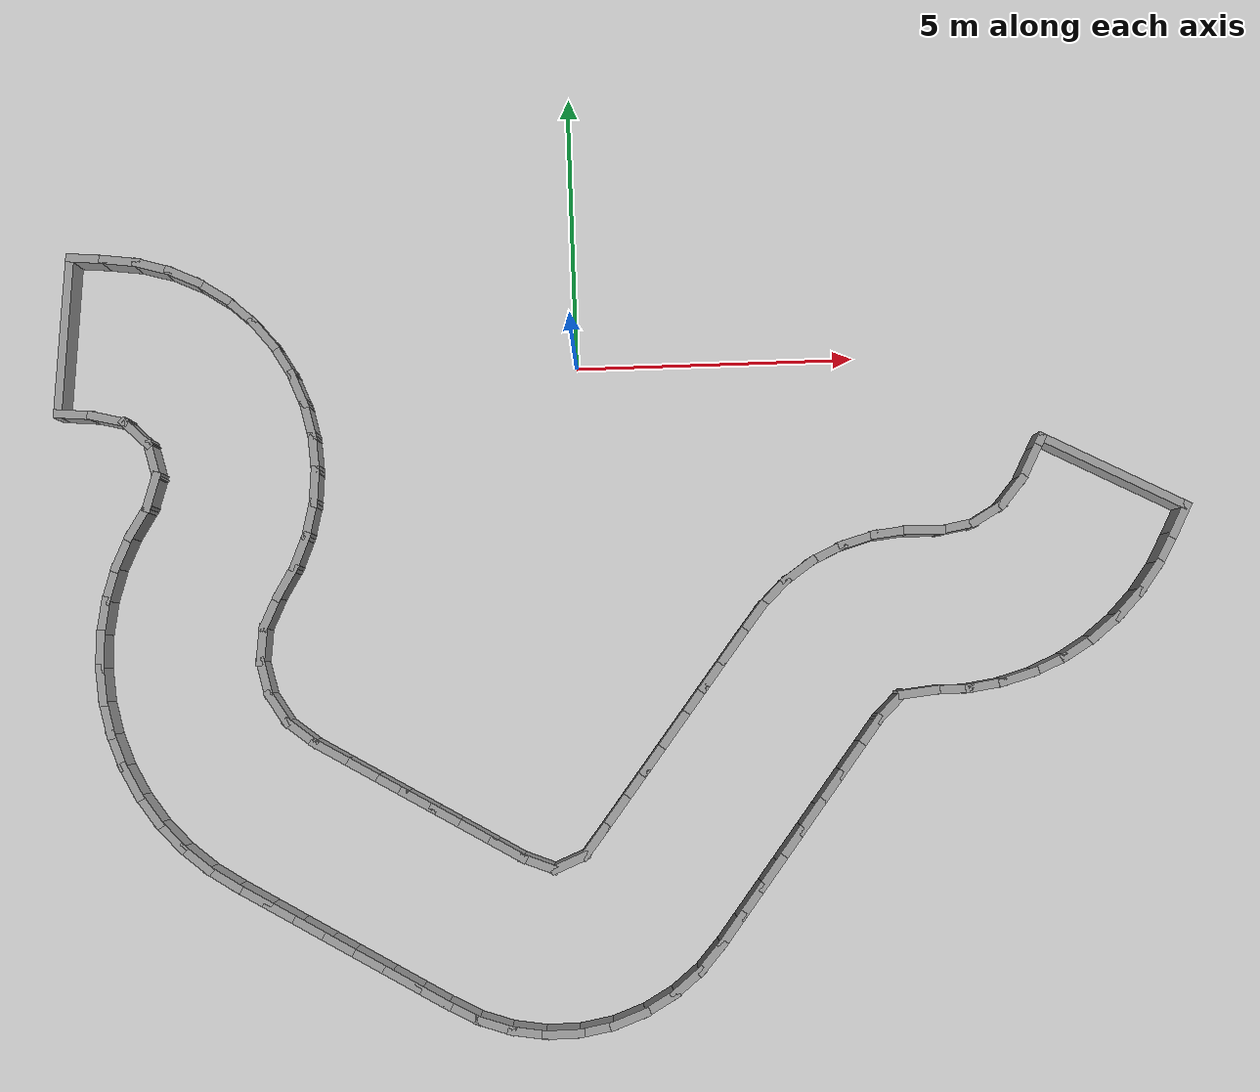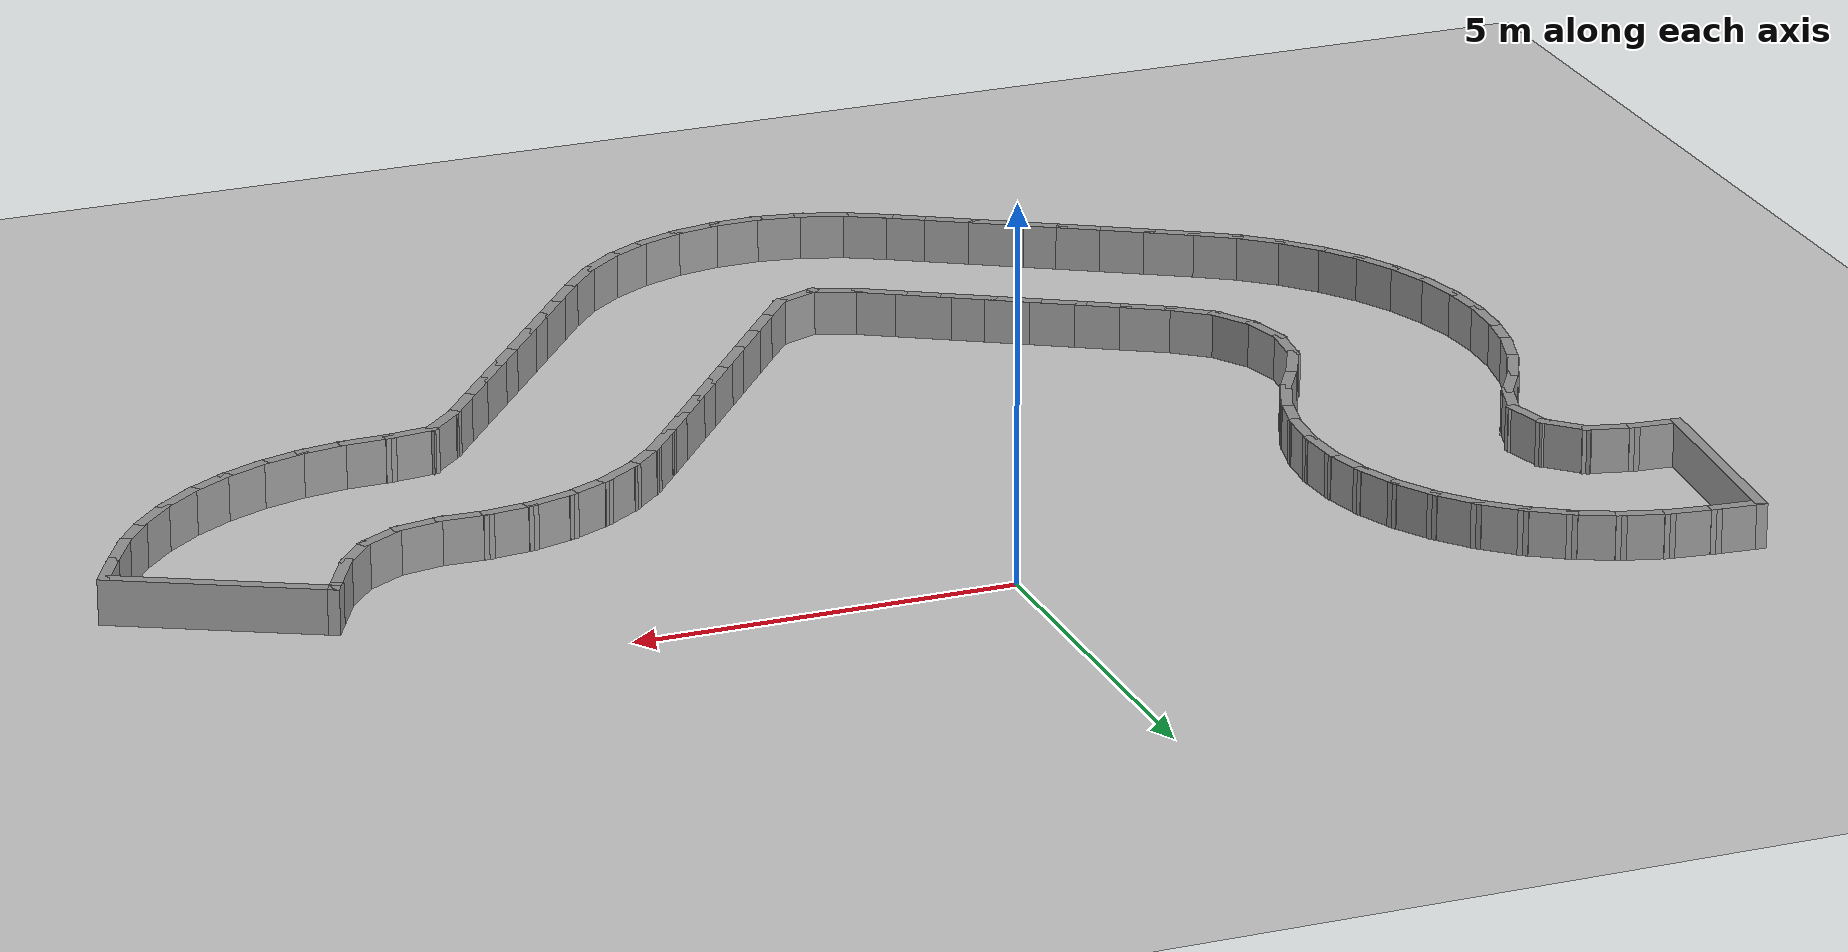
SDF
<?xml version="1.0" ?>
<sdf version='1.7'>
  <world name='default'>
    <plugin name='gazebo_ros_state' filename='libgazebo_ros_state.so'>
      <ros>
        <namespace>/</namespace>
      </ros>
      <update_rate>1000.0</update_rate>
    </plugin>

    <light name='sun' type='directional'>
      <cast_shadows>1</cast_shadows>
      <pose>0 0 10 0 -0 0</pose>
      <diffuse>0.8 0.8 0.8 1</diffuse>
      <specular>0.2 0.2 0.2 1</specular>
      <attenuation>
        <range>1000</range>
        <constant>0.9</constant>
        <linear>0.01</linear>
        <quadratic>0.001</quadratic>
      </attenuation>
      <direction>-0.5 0.1 -0.9</direction>
      <spot>
        <inner_angle>0</inner_angle>
        <outer_angle>0</outer_angle>
        <falloff>0</falloff>
      </spot>
    </light>
    <model name='ground_plane'>
      <static>1</static>
      <link name='link'>
        <collision name='collision'>
          <geometry>
            <plane>
              <normal>0 0 1</normal>
              <size>100 100</size>
            </plane>
          </geometry>
          <surface>
            <friction>
              <ode>
                <mu>100</mu>
                <mu2>50</mu2>
              </ode>
              <torsional>
                <ode/>
              </torsional>
            </friction>
            <contact>
              <ode/>
            </contact>
            <bounce/>
          </surface>
          <max_contacts>10</max_contacts>
        </collision>
        <visual name='visual'>
          <cast_shadows>0</cast_shadows>
          <geometry>
            <plane>
              <normal>0 0 1</normal>
              <size>100 100</size>
            </plane>
          </geometry>
          <material>
            <script>
              <uri>file://media/materials/scripts/gazebo.material</uri>
              <name>Gazebo/Grey</name>
            </script>
          </material>
        </visual>
        <self_collide>0</self_collide>
        <enable_wind>0</enable_wind>
        <kinematic>0</kinematic>
      </link>
    </model>
    <gravity>0 0 -9.8</gravity>
    <magnetic_field>6e-06 2.3e-05 -4.2e-05</magnetic_field>
    <atmosphere type='adiabatic'/>
    <physics type='ode'>
      <max_step_size>0.001</max_step_size>
      <real_time_factor>1</real_time_factor>
      <real_time_update_rate>1000</real_time_update_rate>
    </physics>
    <scene>
      <ambient>0.4 0.4 0.4 1</ambient>
      <background>0.7 0.7 0.7 1</background>
      <shadows>1</shadows>
    </scene>
    <audio>
      <device>default</device>
    </audio>
    <wind/>
    <spherical_coordinates>
      <surface_model>EARTH_WGS84</surface_model>
      <latitude_deg>0</latitude_deg>
      <longitude_deg>0</longitude_deg>
      <elevation>0</elevation>
      <heading_deg>0</heading_deg>
    </spherical_coordinates>
  <model name='rand_turn_05'>
    <pose>0 0 0 0 -0 0</pose>
    <link name='Wall_0'>
      <collision name='Wall_0_Collision'>
        <geometry><box><size>0.7500 0.1500 0.6000</size></box></geometry>
        <pose>0 0 0.3000 0 -0 0</pose>
      </collision>
      <visual name='Wall_0_Visual'>
        <pose>0 0 0.3000 0 -0 0</pose>
        <geometry><box><size>0.7500 0.1500 0.6000</size></box></geometry>
        <material>
          <script>
            <uri>file://media/materials/scripts/gazebo.material</uri>
            <name>Gazebo/Grey</name>
          </script>
          <ambient>1 1 1 1</ambient>
        </material>
      </visual>
      <pose>-8.7626 2.2049 0 0 -0 -0.08479</pose>
    </link>
    <link name='Wall_1'>
      <collision name='Wall_1_Collision'>
        <geometry><box><size>0.7495 0.1500 0.6000</size></box></geometry>
        <pose>0 0 0.3000 0 -0 0</pose>
      </collision>
      <visual name='Wall_1_Visual'>
        <pose>0 0 0.3000 0 -0 0</pose>
        <geometry><box><size>0.7495 0.1500 0.6000</size></box></geometry>
        <material>
          <script>
            <uri>file://media/materials/scripts/gazebo.material</uri>
            <name>Gazebo/Grey</name>
          </script>
          <ambient>1 1 1 1</ambient>
        </material>
      </visual>
      <pose>-8.1663 2.1412 0 0 -0 -0.12813</pose>
    </link>
    <link name='Wall_2'>
      <collision name='Wall_2_Collision'>
        <geometry><box><size>0.7494 0.1500 0.6000</size></box></geometry>
        <pose>0 0 0.3000 0 -0 0</pose>
      </collision>
      <visual name='Wall_2_Visual'>
        <pose>0 0 0.3000 0 -0 0</pose>
        <geometry><box><size>0.7494 0.1500 0.6000</size></box></geometry>
        <material>
          <script>
            <uri>file://media/materials/scripts/gazebo.material</uri>
            <name>Gazebo/Grey</name>
          </script>
          <ambient>1 1 1 1</ambient>
        </material>
      </visual>
      <pose>-7.5807 2.0215 0 0 -0 -0.27534</pose>
    </link>
    <link name='Wall_3'>
      <collision name='Wall_3_Collision'>
        <geometry><box><size>0.7494 0.1500 0.6000</size></box></geometry>
        <pose>0 0 0.3000 0 -0 0</pose>
      </collision>
      <visual name='Wall_3_Visual'>
        <pose>0 0 0.3000 0 -0 0</pose>
        <geometry><box><size>0.7494 0.1500 0.6000</size></box></geometry>
        <material>
          <script>
            <uri>file://media/materials/scripts/gazebo.material</uri>
            <name>Gazebo/Grey</name>
          </script>
          <ambient>1 1 1 1</ambient>
        </material>
      </visual>
      <pose>-7.0196 1.8156 0 0 -0 -0.42779</pose>
    </link>
    <link name='Wall_4'>
      <collision name='Wall_4_Collision'>
        <geometry><box><size>0.7494 0.1500 0.6000</size></box></geometry>
        <pose>0 0 0.3000 0 -0 0</pose>
      </collision>
      <visual name='Wall_4_Visual'>
        <pose>0 0 0.3000 0 -0 0</pose>
        <geometry><box><size>0.7494 0.1500 0.6000</size></box></geometry>
        <material>
          <script>
            <uri>file://media/materials/scripts/gazebo.material</uri>
            <name>Gazebo/Grey</name>
          </script>
          <ambient>1 1 1 1</ambient>
        </material>
      </visual>
      <pose>-6.4964 1.5267 0 0 -0 -0.58156</pose>
    </link>
    <link name='Wall_5'>
      <collision name='Wall_5_Collision'>
        <geometry><box><size>0.7494 0.1500 0.6000</size></box></geometry>
        <pose>0 0 0.3000 0 -0 0</pose>
      </collision>
      <visual name='Wall_5_Visual'>
        <pose>0 0 0.3000 0 -0 0</pose>
        <geometry><box><size>0.7494 0.1500 0.6000</size></box></geometry>
        <material>
          <script>
            <uri>file://media/materials/scripts/gazebo.material</uri>
            <name>Gazebo/Grey</name>
          </script>
          <ambient>1 1 1 1</ambient>
        </material>
      </visual>
      <pose>-6.0235 1.1612 0 0 -0 -0.73442</pose>
    </link>
    <link name='Wall_6'>
      <collision name='Wall_6_Collision'>
        <geometry><box><size>0.7493 0.1500 0.6000</size></box></geometry>
        <pose>0 0 0.3000 0 -0 0</pose>
      </collision>
      <visual name='Wall_6_Visual'>
        <pose>0 0 0.3000 0 -0 0</pose>
        <geometry><box><size>0.7493 0.1500 0.6000</size></box></geometry>
        <material>
          <script>
            <uri>file://media/materials/scripts/gazebo.material</uri>
            <name>Gazebo/Grey</name>
          </script>
          <ambient>1 1 1 1</ambient>
        </material>
      </visual>
      <pose>-5.6118 0.7281 0 0 -0 -0.88686</pose>
    </link>
    <link name='Wall_7'>
      <collision name='Wall_7_Collision'>
        <geometry><box><size>0.7493 0.1500 0.6000</size></box></geometry>
        <pose>0 0 0.3000 0 -0 0</pose>
      </collision>
      <visual name='Wall_7_Visual'>
        <pose>0 0 0.3000 0 -0 0</pose>
        <geometry><box><size>0.7493 0.1500 0.6000</size></box></geometry>
        <material>
          <script>
            <uri>file://media/materials/scripts/gazebo.material</uri>
            <name>Gazebo/Grey</name>
          </script>
          <ambient>1 1 1 1</ambient>
        </material>
      </visual>
      <pose>-5.2705 0.2375 0 0 -0 -1.03931</pose>
    </link>
    <link name='Wall_8'>
      <collision name='Wall_8_Collision'>
        <geometry><box><size>0.7494 0.1500 0.6000</size></box></geometry>
        <pose>0 0 0.3000 0 -0 0</pose>
      </collision>
      <visual name='Wall_8_Visual'>
        <pose>0 0 0.3000 0 -0 0</pose>
        <geometry><box><size>0.7494 0.1500 0.6000</size></box></geometry>
        <material>
          <script>
            <uri>file://media/materials/scripts/gazebo.material</uri>
            <name>Gazebo/Grey</name>
          </script>
          <ambient>1 1 1 1</ambient>
        </material>
      </visual>
      <pose>-5.0078 -0.2993 0 0 -0 -1.19175</pose>
    </link>
    <link name='Wall_9'>
      <collision name='Wall_9_Collision'>
        <geometry><box><size>0.7494 0.1500 0.6000</size></box></geometry>
        <pose>0 0 0.3000 0 -0 0</pose>
      </collision>
      <visual name='Wall_9_Visual'>
        <pose>0 0 0.3000 0 -0 0</pose>
        <geometry><box><size>0.7494 0.1500 0.6000</size></box></geometry>
        <material>
          <script>
            <uri>file://media/materials/scripts/gazebo.material</uri>
            <name>Gazebo/Grey</name>
          </script>
          <ambient>1 1 1 1</ambient>
        </material>
      </visual>
      <pose>-4.8295 -0.8697 0 0 -0 -1.34420</pose>
    </link>
    <link name='Wall_10'>
      <collision name='Wall_10_Collision'>
        <geometry><box><size>0.7494 0.1500 0.6000</size></box></geometry>
        <pose>0 0 0.3000 0 -0 0</pose>
      </collision>
      <visual name='Wall_10_Visual'>
        <pose>0 0 0.3000 0 -0 0</pose>
        <geometry><box><size>0.7494 0.1500 0.6000</size></box></geometry>
        <material>
          <script>
            <uri>file://media/materials/scripts/gazebo.material</uri>
            <name>Gazebo/Grey</name>
          </script>
          <ambient>1 1 1 1</ambient>
        </material>
      </visual>
      <pose>-4.7404 -1.4607 0 0 -0 -1.49800</pose>
    </link>
    <link name='Wall_11'>
      <collision name='Wall_11_Collision'>
        <geometry><box><size>0.7494 0.1500 0.6000</size></box></geometry>
        <pose>0 0 0.3000 0 -0 0</pose>
      </collision>
      <visual name='Wall_11_Visual'>
        <pose>0 0 0.3000 0 -0 0</pose>
        <geometry><box><size>0.7494 0.1500 0.6000</size></box></geometry>
        <material>
          <script>
            <uri>file://media/materials/scripts/gazebo.material</uri>
            <name>Gazebo/Grey</name>
          </script>
          <ambient>1 1 1 1</ambient>
        </material>
      </visual>
      <pose>-4.7426 -2.0583 0 0 -0 -1.65083</pose>
    </link>
    <link name='Wall_12'>
      <collision name='Wall_12_Collision'>
        <geometry><box><size>0.7493 0.1500 0.6000</size></box></geometry>
        <pose>0 0 0.3000 0 -0 0</pose>
      </collision>
      <visual name='Wall_12_Visual'>
        <pose>0 0 0.3000 0 -0 0</pose>
        <geometry><box><size>0.7493 0.1500 0.6000</size></box></geometry>
        <material>
          <script>
            <uri>file://media/materials/scripts/gazebo.material</uri>
            <name>Gazebo/Grey</name>
          </script>
          <ambient>1 1 1 1</ambient>
        </material>
      </visual>
      <pose>-4.8356 -2.6487 0 0 -0 -1.80327</pose>
    </link>
    <link name='Wall_13'>
      <collision name='Wall_13_Collision'>
        <geometry><box><size>0.7493 0.1500 0.6000</size></box></geometry>
        <pose>0 0 0.3000 0 -0 0</pose>
      </collision>
      <visual name='Wall_13_Visual'>
        <pose>0 0 0.3000 0 -0 0</pose>
        <geometry><box><size>0.7493 0.1500 0.6000</size></box></geometry>
        <material>
          <script>
            <uri>file://media/materials/scripts/gazebo.material</uri>
            <name>Gazebo/Grey</name>
          </script>
          <ambient>1 1 1 1</ambient>
        </material>
      </visual>
      <pose>-5.0171 -3.2180 0 0 -0 -1.95572</pose>
    </link>
    <link name='Wall_14'>
      <collision name='Wall_14_Collision'>
        <geometry><box><size>0.7494 0.1500 0.6000</size></box></geometry>
        <pose>0 0 0.3000 0 -0 0</pose>
      </collision>
      <visual name='Wall_14_Visual'>
        <pose>0 0 0.3000 0 -0 0</pose>
        <geometry><box><size>0.7494 0.1500 0.6000</size></box></geometry>
        <material>
          <script>
            <uri>file://media/materials/scripts/gazebo.material</uri>
            <name>Gazebo/Grey</name>
          </script>
          <ambient>1 1 1 1</ambient>
        </material>
      </visual>
      <pose>-5.2828 -3.7534 0 0 -0 -2.10714</pose>
    </link>
    <link name='Wall_15'>
      <collision name='Wall_15_Collision'>
        <geometry><box><size>0.7472 0.1500 0.6000</size></box></geometry>
        <pose>0 0 0.3000 0 -0 0</pose>
      </collision>
      <visual name='Wall_15_Visual'>
        <pose>0 0 0.3000 0 -0 0</pose>
        <geometry><box><size>0.7472 0.1500 0.6000</size></box></geometry>
        <material>
          <script>
            <uri>file://media/materials/scripts/gazebo.material</uri>
            <name>Gazebo/Grey</name>
          </script>
          <ambient>1 1 1 1</ambient>
        </material>
      </visual>
      <pose>-5.5640 -4.2807 0 0 -0 -2.01420</pose>
    </link>
    <link name='Wall_16'>
      <collision name='Wall_16_Collision'>
        <geometry><box><size>0.7472 0.1500 0.6000</size></box></geometry>
        <pose>0 0 0.3000 0 -0 0</pose>
      </collision>
      <visual name='Wall_16_Visual'>
        <pose>0 0 0.3000 0 -0 0</pose>
        <geometry><box><size>0.7472 0.1500 0.6000</size></box></geometry>
        <material>
          <script>
            <uri>file://media/materials/scripts/gazebo.material</uri>
            <name>Gazebo/Grey</name>
          </script>
          <ambient>1 1 1 1</ambient>
        </material>
      </visual>
      <pose>-5.7241 -4.8473 0 0 -0 -1.67809</pose>
    </link>
    <link name='Wall_17'>
      <collision name='Wall_17_Collision'>
        <geometry><box><size>0.7472 0.1500 0.6000</size></box></geometry>
        <pose>0 0 0.3000 0 -0 0</pose>
      </collision>
      <visual name='Wall_17_Visual'>
        <pose>0 0 0.3000 0 -0 0</pose>
        <geometry><box><size>0.7472 0.1500 0.6000</size></box></geometry>
        <material>
          <script>
            <uri>file://media/materials/scripts/gazebo.material</uri>
            <name>Gazebo/Grey</name>
          </script>
          <ambient>1 1 1 1</ambient>
        </material>
      </visual>
      <pose>-5.6886 -5.4350 0 0 -0 -1.34269</pose>
    </link>
    <link name='Wall_18'>
      <collision name='Wall_18_Collision'>
        <geometry><box><size>0.7471 0.1500 0.6000</size></box></geometry>
        <pose>0 0 0.3000 0 -0 0</pose>
      </collision>
      <visual name='Wall_18_Visual'>
        <pose>0 0 0.3000 0 -0 0</pose>
        <geometry><box><size>0.7471 0.1500 0.6000</size></box></geometry>
        <material>
          <script>
            <uri>file://media/materials/scripts/gazebo.material</uri>
            <name>Gazebo/Grey</name>
          </script>
          <ambient>1 1 1 1</ambient>
        </material>
      </visual>
      <pose>-5.4616 -5.9783 0 0 -0 -1.00732</pose>
    </link>
    <link name='Wall_19'>
      <collision name='Wall_19_Collision'>
        <geometry><box><size>0.7473 0.1500 0.6000</size></box></geometry>
        <pose>0 0 0.3000 0 -0 0</pose>
      </collision>
      <visual name='Wall_19_Visual'>
        <pose>0 0 0.3000 0 -0 0</pose>
        <geometry><box><size>0.7473 0.1500 0.6000</size></box></geometry>
        <material>
          <script>
            <uri>file://media/materials/scripts/gazebo.material</uri>
            <name>Gazebo/Grey</name>
          </script>
          <ambient>1 1 1 1</ambient>
        </material>
      </visual>
      <pose>-5.0686 -6.4169 0 0 -0 -0.67321</pose>
    </link>
    <link name='Wall_20'>
      <collision name='Wall_20_Collision'>
        <geometry><box><size>0.7500 0.1500 0.6000</size></box></geometry>
        <pose>0 0 0.3000 0 -0 0</pose>
      </collision>
      <visual name='Wall_20_Visual'>
        <pose>0 0 0.3000 0 -0 0</pose>
        <geometry><box><size>0.7500 0.1500 0.6000</size></box></geometry>
        <material>
          <script>
            <uri>file://media/materials/scripts/gazebo.material</uri>
            <name>Gazebo/Grey</name>
          </script>
          <ambient>1 1 1 1</ambient>
        </material>
      </visual>
      <pose>-4.5766 -6.7553 0 0 -0 -0.53219</pose>
    </link>
    <link name='Wall_21'>
      <collision name='Wall_21_Collision'>
        <geometry><box><size>0.7500 0.1500 0.6000</size></box></geometry>
        <pose>0 0 0.3000 0 -0 0</pose>
      </collision>
      <visual name='Wall_21_Visual'>
        <pose>0 0 0.3000 0 -0 0</pose>
        <geometry><box><size>0.7500 0.1500 0.6000</size></box></geometry>
        <material>
          <script>
            <uri>file://media/materials/scripts/gazebo.material</uri>
            <name>Gazebo/Grey</name>
          </script>
          <ambient>1 1 1 1</ambient>
        </material>
      </visual>
      <pose>-4.0596 -7.0598 0 0 -0 -0.53224</pose>
    </link>
    <link name='Wall_22'>
      <collision name='Wall_22_Collision'>
        <geometry><box><size>0.7500 0.1500 0.6000</size></box></geometry>
        <pose>0 0 0.3000 0 -0 0</pose>
      </collision>
      <visual name='Wall_22_Visual'>
        <pose>0 0 0.3000 0 -0 0</pose>
        <geometry><box><size>0.7500 0.1500 0.6000</size></box></geometry>
        <material>
          <script>
            <uri>file://media/materials/scripts/gazebo.material</uri>
            <name>Gazebo/Grey</name>
          </script>
          <ambient>1 1 1 1</ambient>
        </material>
      </visual>
      <pose>-3.5426 -7.3643 0 0 -0 -0.53224</pose>
    </link>
    <link name='Wall_23'>
      <collision name='Wall_23_Collision'>
        <geometry><box><size>0.7500 0.1500 0.6000</size></box></geometry>
        <pose>0 0 0.3000 0 -0 0</pose>
      </collision>
      <visual name='Wall_23_Visual'>
        <pose>0 0 0.3000 0 -0 0</pose>
        <geometry><box><size>0.7500 0.1500 0.6000</size></box></geometry>
        <material>
          <script>
            <uri>file://media/materials/scripts/gazebo.material</uri>
            <name>Gazebo/Grey</name>
          </script>
          <ambient>1 1 1 1</ambient>
        </material>
      </visual>
      <pose>-3.0256 -7.6688 0 0 -0 -0.53224</pose>
    </link>
    <link name='Wall_24'>
      <collision name='Wall_24_Collision'>
        <geometry><box><size>0.7500 0.1500 0.6000</size></box></geometry>
        <pose>0 0 0.3000 0 -0 0</pose>
      </collision>
      <visual name='Wall_24_Visual'>
        <pose>0 0 0.3000 0 -0 0</pose>
        <geometry><box><size>0.7500 0.1500 0.6000</size></box></geometry>
        <material>
          <script>
            <uri>file://media/materials/scripts/gazebo.material</uri>
            <name>Gazebo/Grey</name>
          </script>
          <ambient>1 1 1 1</ambient>
        </material>
      </visual>
      <pose>-2.5086 -7.9733 0 0 -0 -0.53224</pose>
    </link>
    <link name='Wall_25'>
      <collision name='Wall_25_Collision'>
        <geometry><box><size>0.7500 0.1500 0.6000</size></box></geometry>
        <pose>0 0 0.3000 0 -0 0</pose>
      </collision>
      <visual name='Wall_25_Visual'>
        <pose>0 0 0.3000 0 -0 0</pose>
        <geometry><box><size>0.7500 0.1500 0.6000</size></box></geometry>
        <material>
          <script>
            <uri>file://media/materials/scripts/gazebo.material</uri>
            <name>Gazebo/Grey</name>
          </script>
          <ambient>1 1 1 1</ambient>
        </material>
      </visual>
      <pose>-1.9916 -8.2777 0 0 -0 -0.53224</pose>
    </link>
    <link name='Wall_26'>
      <collision name='Wall_26_Collision'>
        <geometry><box><size>0.7500 0.1500 0.6000</size></box></geometry>
        <pose>0 0 0.3000 0 -0 0</pose>
      </collision>
      <visual name='Wall_26_Visual'>
        <pose>0 0 0.3000 0 -0 0</pose>
        <geometry><box><size>0.7500 0.1500 0.6000</size></box></geometry>
        <material>
          <script>
            <uri>file://media/materials/scripts/gazebo.material</uri>
            <name>Gazebo/Grey</name>
          </script>
          <ambient>1 1 1 1</ambient>
        </material>
      </visual>
      <pose>-1.4746 -8.5822 0 0 -0 -0.53224</pose>
    </link>
    <link name='Wall_27'>
      <collision name='Wall_27_Collision'>
        <geometry><box><size>0.7416 0.1500 0.6000</size></box></geometry>
        <pose>0 0 0.3000 0 -0 0</pose>
      </collision>
      <visual name='Wall_27_Visual'>
        <pose>0 0 0.3000 0 -0 0</pose>
        <geometry><box><size>0.7416 0.1500 0.6000</size></box></geometry>
        <material>
          <script>
            <uri>file://media/materials/scripts/gazebo.material</uri>
            <name>Gazebo/Grey</name>
          </script>
          <ambient>1 1 1 1</ambient>
        </material>
      </visual>
      <pose>-0.9412 -8.8438 0 0 -0 -0.37850</pose>
    </link>
    <link name='Wall_28'>
      <collision name='Wall_28_Collision'>
        <geometry><box><size>0.7329 0.1500 0.6000</size></box></geometry>
        <pose>0 0 0.3000 0 -0 0</pose>
      </collision>
      <visual name='Wall_28_Visual'>
        <pose>0 0 0.3000 0 -0 0</pose>
        <geometry><box><size>0.7329 0.1500 0.6000</size></box></geometry>
        <material>
          <script>
            <uri>file://media/materials/scripts/gazebo.material</uri>
            <name>Gazebo/Grey</name>
          </script>
          <ambient>1 1 1 1</ambient>
        </material>
      </visual>
      <pose>-0.3967 -8.8427 0 0 -0 0.38835</pose>
    </link>
    <link name='Wall_29'>
      <collision name='Wall_29_Collision'>
        <geometry><box><size>0.7498 0.1500 0.6000</size></box></geometry>
        <pose>0 0 0.3000 0 -0 0</pose>
      </collision>
      <visual name='Wall_29_Visual'>
        <pose>0 0 0.3000 0 -0 0</pose>
        <geometry><box><size>0.7498 0.1500 0.6000</size></box></geometry>
        <material>
          <script>
            <uri>file://media/materials/scripts/gazebo.material</uri>
            <name>Gazebo/Grey</name>
          </script>
          <ambient>1 1 1 1</ambient>
        </material>
      </visual>
      <pose>0.0571 -8.4955 0 0 -0 0.91026</pose>
    </link>
    <link name='Wall_30'>
      <collision name='Wall_30_Collision'>
        <geometry><box><size>0.7500 0.1500 0.6000</size></box></geometry>
        <pose>0 0 0.3000 0 -0 0</pose>
      </collision>
      <visual name='Wall_30_Visual'>
        <pose>0 0 0.3000 0 -0 0</pose>
        <geometry><box><size>0.7500 0.1500 0.6000</size></box></geometry>
        <material>
          <script>
            <uri>file://media/materials/scripts/gazebo.material</uri>
            <name>Gazebo/Grey</name>
          </script>
          <ambient>1 1 1 1</ambient>
        </material>
      </visual>
      <pose>0.4232 -8.0203 0 0 -0 0.91858</pose>
    </link>
    <link name='Wall_31'>
      <collision name='Wall_31_Collision'>
        <geometry><box><size>0.7500 0.1500 0.6000</size></box></geometry>
        <pose>0 0 0.3000 0 -0 0</pose>
      </collision>
      <visual name='Wall_31_Visual'>
        <pose>0 0 0.3000 0 -0 0</pose>
        <geometry><box><size>0.7500 0.1500 0.6000</size></box></geometry>
        <material>
          <script>
            <uri>file://media/materials/scripts/gazebo.material</uri>
            <name>Gazebo/Grey</name>
          </script>
          <ambient>1 1 1 1</ambient>
        </material>
      </visual>
      <pose>0.7873 -7.5434 0 0 -0 0.91858</pose>
    </link>
    <link name='Wall_32'>
      <collision name='Wall_32_Collision'>
        <geometry><box><size>0.7500 0.1500 0.6000</size></box></geometry>
        <pose>0 0 0.3000 0 -0 0</pose>
      </collision>
      <visual name='Wall_32_Visual'>
        <pose>0 0 0.3000 0 -0 0</pose>
        <geometry><box><size>0.7500 0.1500 0.6000</size></box></geometry>
        <material>
          <script>
            <uri>file://media/materials/scripts/gazebo.material</uri>
            <name>Gazebo/Grey</name>
          </script>
          <ambient>1 1 1 1</ambient>
        </material>
      </visual>
      <pose>1.1515 -7.0666 0 0 -0 0.91858</pose>
    </link>
    <link name='Wall_33'>
      <collision name='Wall_33_Collision'>
        <geometry><box><size>0.7500 0.1500 0.6000</size></box></geometry>
        <pose>0 0 0.3000 0 -0 0</pose>
      </collision>
      <visual name='Wall_33_Visual'>
        <pose>0 0 0.3000 0 -0 0</pose>
        <geometry><box><size>0.7500 0.1500 0.6000</size></box></geometry>
        <material>
          <script>
            <uri>file://media/materials/scripts/gazebo.material</uri>
            <name>Gazebo/Grey</name>
          </script>
          <ambient>1 1 1 1</ambient>
        </material>
      </visual>
      <pose>1.5157 -6.5897 0 0 -0 0.91858</pose>
    </link>
    <link name='Wall_34'>
      <collision name='Wall_34_Collision'>
        <geometry><box><size>0.7500 0.1500 0.6000</size></box></geometry>
        <pose>0 0 0.3000 0 -0 0</pose>
      </collision>
      <visual name='Wall_34_Visual'>
        <pose>0 0 0.3000 0 -0 0</pose>
        <geometry><box><size>0.7500 0.1500 0.6000</size></box></geometry>
        <material>
          <script>
            <uri>file://media/materials/scripts/gazebo.material</uri>
            <name>Gazebo/Grey</name>
          </script>
          <ambient>1 1 1 1</ambient>
        </material>
      </visual>
      <pose>1.8799 -6.1129 0 0 -0 0.91858</pose>
    </link>
    <link name='Wall_35'>
      <collision name='Wall_35_Collision'>
        <geometry><box><size>0.7500 0.1500 0.6000</size></box></geometry>
        <pose>0 0 0.3000 0 -0 0</pose>
      </collision>
      <visual name='Wall_35_Visual'>
        <pose>0 0 0.3000 0 -0 0</pose>
        <geometry><box><size>0.7500 0.1500 0.6000</size></box></geometry>
        <material>
          <script>
            <uri>file://media/materials/scripts/gazebo.material</uri>
            <name>Gazebo/Grey</name>
          </script>
          <ambient>1 1 1 1</ambient>
        </material>
      </visual>
      <pose>2.2440 -5.6360 0 0 -0 0.91858</pose>
    </link>
    <link name='Wall_36'>
      <collision name='Wall_36_Collision'>
        <geometry><box><size>0.7500 0.1500 0.6000</size></box></geometry>
        <pose>0 0 0.3000 0 -0 0</pose>
      </collision>
      <visual name='Wall_36_Visual'>
        <pose>0 0 0.3000 0 -0 0</pose>
        <geometry><box><size>0.7500 0.1500 0.6000</size></box></geometry>
        <material>
          <script>
            <uri>file://media/materials/scripts/gazebo.material</uri>
            <name>Gazebo/Grey</name>
          </script>
          <ambient>1 1 1 1</ambient>
        </material>
      </visual>
      <pose>2.6082 -5.1592 0 0 -0 0.91858</pose>
    </link>
    <link name='Wall_37'>
      <collision name='Wall_37_Collision'>
        <geometry><box><size>0.7499 0.1500 0.6000</size></box></geometry>
        <pose>0 0 0.3000 0 -0 0</pose>
      </collision>
      <visual name='Wall_37_Visual'>
        <pose>0 0 0.3000 0 -0 0</pose>
        <geometry><box><size>0.7499 0.1500 0.6000</size></box></geometry>
        <material>
          <script>
            <uri>file://media/materials/scripts/gazebo.material</uri>
            <name>Gazebo/Grey</name>
          </script>
          <ambient>1 1 1 1</ambient>
        </material>
      </visual>
      <pose>2.9754 -4.6848 0 0 -0 0.90558</pose>
    </link>
    <link name='Wall_38'>
      <collision name='Wall_38_Collision'>
        <geometry><box><size>0.7493 0.1500 0.6000</size></box></geometry>
        <pose>0 0 0.3000 0 -0 0</pose>
      </collision>
      <visual name='Wall_38_Visual'>
        <pose>0 0 0.3000 0 -0 0</pose>
        <geometry><box><size>0.7493 0.1500 0.6000</size></box></geometry>
        <material>
          <script>
            <uri>file://media/materials/scripts/gazebo.material</uri>
            <name>Gazebo/Grey</name>
          </script>
          <ambient>1 1 1 1</ambient>
        </material>
      </visual>
      <pose>3.3745 -4.2390 0 0 -0 0.77561</pose>
    </link>
    <link name='Wall_39'>
      <collision name='Wall_39_Collision'>
        <geometry><box><size>0.7493 0.1500 0.6000</size></box></geometry>
        <pose>0 0 0.3000 0 -0 0</pose>
      </collision>
      <visual name='Wall_39_Visual'>
        <pose>0 0 0.3000 0 -0 0</pose>
        <geometry><box><size>0.7493 0.1500 0.6000</size></box></geometry>
        <material>
          <script>
            <uri>file://media/materials/scripts/gazebo.material</uri>
            <name>Gazebo/Grey</name>
          </script>
          <ambient>1 1 1 1</ambient>
        </material>
      </visual>
      <pose>3.8343 -3.8580 0 0 -0 0.60832</pose>
    </link>
    <link name='Wall_40'>
      <collision name='Wall_40_Collision'>
        <geometry><box><size>0.7492 0.1500 0.6000</size></box></geometry>
        <pose>0 0 0.3000 0 -0 0</pose>
      </collision>
      <visual name='Wall_40_Visual'>
        <pose>0 0 0.3000 0 -0 0</pose>
        <geometry><box><size>0.7492 0.1500 0.6000</size></box></geometry>
        <material>
          <script>
            <uri>file://media/materials/scripts/gazebo.material</uri>
            <name>Gazebo/Grey</name>
          </script>
          <ambient>1 1 1 1</ambient>
        </material>
      </visual>
      <pose>4.3507 -3.5579 0 0 -0 0.44445</pose>
    </link>
    <link name='Wall_41'>
      <collision name='Wall_41_Collision'>
        <geometry><box><size>0.7493 0.1500 0.6000</size></box></geometry>
        <pose>0 0 0.3000 0 -0 0</pose>
      </collision>
      <visual name='Wall_41_Visual'>
        <pose>0 0 0.3000 0 -0 0</pose>
        <geometry><box><size>0.7493 0.1500 0.6000</size></box></geometry>
        <material>
          <script>
            <uri>file://media/materials/scripts/gazebo.material</uri>
            <name>Gazebo/Grey</name>
          </script>
          <ambient>1 1 1 1</ambient>
        </material>
      </visual>
      <pose>4.9091 -3.3460 0 0 -0 0.28096</pose>
    </link>
    <link name='Wall_42'>
      <collision name='Wall_42_Collision'>
        <geometry><box><size>0.7493 0.1500 0.6000</size></box></geometry>
        <pose>0 0 0.3000 0 -0 0</pose>
      </collision>
      <visual name='Wall_42_Visual'>
        <pose>0 0 0.3000 0 -0 0</pose>
        <geometry><box><size>0.7493 0.1500 0.6000</size></box></geometry>
        <material>
          <script>
            <uri>file://media/materials/scripts/gazebo.material</uri>
            <name>Gazebo/Grey</name>
          </script>
          <ambient>1 1 1 1</ambient>
        </material>
      </visual>
      <pose>5.4948 -3.2290 0 0 -0 0.11343</pose>
    </link>
    <link name='Wall_43'>
      <collision name='Wall_43_Collision'>
        <geometry><box><size>0.7496 0.1500 0.6000</size></box></geometry>
        <pose>0 0 0.3000 0 -0 0</pose>
      </collision>
      <visual name='Wall_43_Visual'>
        <pose>0 0 0.3000 0 -0 0</pose>
        <geometry><box><size>0.7496 0.1500 0.6000</size></box></geometry>
        <material>
          <script>
            <uri>file://media/materials/scripts/gazebo.material</uri>
            <name>Gazebo/Grey</name>
          </script>
          <ambient>1 1 1 1</ambient>
        </material>
      </visual>
      <pose>6.0922 -3.2042 0 0 -0 -0.03039</pose>
    </link>
    <link name='Wall_44'>
      <collision name='Wall_44_Collision'>
        <geometry><box><size>0.7470 0.1500 0.6000</size></box></geometry>
        <pose>0 0 0.3000 0 -0 0</pose>
      </collision>
      <visual name='Wall_44_Visual'>
        <pose>0 0 0.3000 0 -0 0</pose>
        <geometry><box><size>0.7470 0.1500 0.6000</size></box></geometry>
        <material>
          <script>
            <uri>file://media/materials/scripts/gazebo.material</uri>
            <name>Gazebo/Grey</name>
          </script>
          <ambient>1 1 1 1</ambient>
        </material>
      </visual>
      <pose>6.6855 -3.1601 0 0 -0 0.17923</pose>
    </link>
    <link name='Wall_45'>
      <collision name='Wall_45_Collision'>
        <geometry><box><size>0.7470 0.1500 0.6000</size></box></geometry>
        <pose>0 0 0.3000 0 -0 0</pose>
      </collision>
      <visual name='Wall_45_Visual'>
        <pose>0 0 0.3000 0 -0 0</pose>
        <geometry><box><size>0.7470 0.1500 0.6000</size></box></geometry>
        <material>
          <script>
            <uri>file://media/materials/scripts/gazebo.material</uri>
            <name>Gazebo/Grey</name>
          </script>
          <ambient>1 1 1 1</ambient>
        </material>
      </visual>
      <pose>7.2375 -2.9572 0 0 -0 0.52534</pose>
    </link>
    <link name='Wall_46'>
      <collision name='Wall_46_Collision'>
        <geometry><box><size>0.7470 0.1500 0.6000</size></box></geometry>
        <pose>0 0 0.3000 0 -0 0</pose>
      </collision>
      <visual name='Wall_46_Visual'>
        <pose>0 0 0.3000 0 -0 0</pose>
        <geometry><box><size>0.7470 0.1500 0.6000</size></box></geometry>
        <material>
          <script>
            <uri>file://media/materials/scripts/gazebo.material</uri>
            <name>Gazebo/Grey</name>
          </script>
          <ambient>1 1 1 1</ambient>
        </material>
      </visual>
      <pose>7.6879 -2.5790 0 0 -0 0.87145</pose>
    </link>
    <link name='Wall_47'>
      <collision name='Wall_47_Collision'>
        <geometry><box><size>0.7500 0.1500 0.6000</size></box></geometry>
        <pose>0 0 0.3000 0 -0 0</pose>
      </collision>
      <visual name='Wall_47_Visual'>
        <pose>0 0 0.3000 0 -0 0</pose>
        <geometry><box><size>0.7500 0.1500 0.6000</size></box></geometry>
        <material>
          <script>
            <uri>file://media/materials/scripts/gazebo.material</uri>
            <name>Gazebo/Grey</name>
          </script>
          <ambient>1 1 1 1</ambient>
        </material>
      </visual>
      <pose>8.0192 -2.0848 0 0 -0 1.08844</pose>
    </link>
    <link name='Wall_48'>
      <collision name='Wall_48_Collision'>
        <geometry><box><size>0.3803 0.1500 0.6000</size></box></geometry>
        <pose>0 0 0.3000 0 -0 0</pose>
      </collision>
      <visual name='Wall_48_Visual'>
        <pose>0 0 0.3000 0 -0 0</pose>
        <geometry><box><size>0.3803 0.1500 0.6000</size></box></geometry>
        <material>
          <script>
            <uri>file://media/materials/scripts/gazebo.material</uri>
            <name>Gazebo/Grey</name>
          </script>
          <ambient>1 1 1 1</ambient>
        </material>
      </visual>
      <pose>8.2115 -1.7169 0 0 -0 1.09093</pose>
    </link>
    <link name='Wall_49'>
      <collision name='Wall_49_Collision'>
        <geometry><box><size>0.7500 0.1500 0.6000</size></box></geometry>
        <pose>0 0 0.3000 0 -0 0</pose>
      </collision>
      <visual name='Wall_49_Visual'>
        <pose>0 0 0.3000 0 -0 0</pose>
        <geometry><box><size>0.7500 0.1500 0.6000</size></box></geometry>
        <material>
          <script>
            <uri>file://media/materials/scripts/gazebo.material</uri>
            <name>Gazebo/Grey</name>
          </script>
          <ambient>1 1 1 1</ambient>
        </material>
      </visual>
      <pose>-9.0029 -0.6232 0 0 -0 -0.08479</pose>
    </link>
    <link name='Wall_50'>
      <collision name='Wall_50_Collision'>
        <geometry><box><size>0.7444 0.1500 0.6000</size></box></geometry>
        <pose>0 0 0.3000 0 -0 0</pose>
      </collision>
      <visual name='Wall_50_Visual'>
        <pose>0 0 0.3000 0 -0 0</pose>
        <geometry><box><size>0.7444 0.1500 0.6000</size></box></geometry>
        <material>
          <script>
            <uri>file://media/materials/scripts/gazebo.material</uri>
            <name>Gazebo/Grey</name>
          </script>
          <ambient>1 1 1 1</ambient>
        </material>
      </visual>
      <pose>-8.4153 -0.7189 0 0 -0 -0.23879</pose>
    </link>
    <link name='Wall_51'>
      <collision name='Wall_51_Collision'>
        <geometry><box><size>0.7424 0.1500 0.6000</size></box></geometry>
        <pose>0 0 0.3000 0 -0 0</pose>
      </collision>
      <visual name='Wall_51_Visual'>
        <pose>0 0 0.3000 0 -0 0</pose>
        <geometry><box><size>0.7424 0.1500 0.6000</size></box></geometry>
        <material>
          <script>
            <uri>file://media/materials/scripts/gazebo.material</uri>
            <name>Gazebo/Grey</name>
          </script>
          <ambient>1 1 1 1</ambient>
        </material>
      </visual>
      <pose>-7.9145 -0.9960 0 0 -0 -0.77289</pose>
    </link>
    <link name='Wall_52'>
      <collision name='Wall_52_Collision'>
        <geometry><box><size>0.7424 0.1500 0.6000</size></box></geometry>
        <pose>0 0 0.3000 0 -0 0</pose>
      </collision>
      <visual name='Wall_52_Visual'>
        <pose>0 0 0.3000 0 -0 0</pose>
        <geometry><box><size>0.7424 0.1500 0.6000</size></box></geometry>
        <material>
          <script>
            <uri>file://media/materials/scripts/gazebo.material</uri>
            <name>Gazebo/Grey</name>
          </script>
          <ambient>1 1 1 1</ambient>
        </material>
      </visual>
      <pose>-7.6298 -1.4900 0 0 -0 -1.32316</pose>
    </link>
    <link name='Wall_53'>
      <collision name='Wall_53_Collision'>
        <geometry><box><size>0.7424 0.1500 0.6000</size></box></geometry>
        <pose>0 0 0.3000 0 -0 0</pose>
      </collision>
      <visual name='Wall_53_Visual'>
        <pose>0 0 0.3000 0 -0 0</pose>
        <geometry><box><size>0.7424 0.1500 0.6000</size></box></geometry>
        <material>
          <script>
            <uri>file://media/materials/scripts/gazebo.material</uri>
            <name>Gazebo/Grey</name>
          </script>
          <ambient>1 1 1 1</ambient>
        </material>
      </visual>
      <pose>-7.6455 -2.0599 0 0 -0 -1.87351</pose>
    </link>
    <link name='Wall_54'>
      <collision name='Wall_54_Collision'>
        <geometry><box><size>0.7496 0.1500 0.6000</size></box></geometry>
        <pose>0 0 0.3000 0 -0 0</pose>
      </collision>
      <visual name='Wall_54_Visual'>
        <pose>0 0 0.3000 0 -0 0</pose>
        <geometry><box><size>0.7496 0.1500 0.6000</size></box></geometry>
        <material>
          <script>
            <uri>file://media/materials/scripts/gazebo.material</uri>
            <name>Gazebo/Grey</name>
          </script>
          <ambient>1 1 1 1</ambient>
        </material>
      </visual>
      <pose>-7.8917 -2.5975 0 0 -0 -2.12550</pose>
    </link>
    <link name='Wall_55'>
      <collision name='Wall_55_Collision'>
        <geometry><box><size>0.7496 0.1500 0.6000</size></box></geometry>
        <pose>0 0 0.3000 0 -0 0</pose>
      </collision>
      <visual name='Wall_55_Visual'>
        <pose>0 0 0.3000 0 -0 0</pose>
        <geometry><box><size>0.7496 0.1500 0.6000</size></box></geometry>
        <material>
          <script>
            <uri>file://media/materials/scripts/gazebo.material</uri>
            <name>Gazebo/Grey</name>
          </script>
          <ambient>1 1 1 1</ambient>
        </material>
      </visual>
      <pose>-8.1736 -3.1253 0 0 -0 -1.99722</pose>
    </link>
    <link name='Wall_56'>
      <collision name='Wall_56_Collision'>
        <geometry><box><size>0.7495 0.1500 0.6000</size></box></geometry>
        <pose>0 0 0.3000 0 -0 0</pose>
      </collision>
      <visual name='Wall_56_Visual'>
        <pose>0 0 0.3000 0 -0 0</pose>
        <geometry><box><size>0.7495 0.1500 0.6000</size></box></geometry>
        <material>
          <script>
            <uri>file://media/materials/scripts/gazebo.material</uri>
            <name>Gazebo/Grey</name>
          </script>
          <ambient>1 1 1 1</ambient>
        </material>
      </visual>
      <pose>-8.3853 -3.6849 0 0 -0 -1.86772</pose>
    </link>
    <link name='Wall_57'>
      <collision name='Wall_57_Collision'>
        <geometry><box><size>0.7495 0.1500 0.6000</size></box></geometry>
        <pose>0 0 0.3000 0 -0 0</pose>
      </collision>
      <visual name='Wall_57_Visual'>
        <pose>0 0 0.3000 0 -0 0</pose>
        <geometry><box><size>0.7495 0.1500 0.6000</size></box></geometry>
        <material>
          <script>
            <uri>file://media/materials/scripts/gazebo.material</uri>
            <name>Gazebo/Grey</name>
          </script>
          <ambient>1 1 1 1</ambient>
        </material>
      </visual>
      <pose>-8.5230 -4.2671 0 0 -0 -1.73822</pose>
    </link>
    <link name='Wall_58'>
      <collision name='Wall_58_Collision'>
        <geometry><box><size>0.7495 0.1500 0.6000</size></box></geometry>
        <pose>0 0 0.3000 0 -0 0</pose>
      </collision>
      <visual name='Wall_58_Visual'>
        <pose>0 0 0.3000 0 -0 0</pose>
        <geometry><box><size>0.7495 0.1500 0.6000</size></box></geometry>
        <material>
          <script>
            <uri>file://media/materials/scripts/gazebo.material</uri>
            <name>Gazebo/Grey</name>
          </script>
          <ambient>1 1 1 1</ambient>
        </material>
      </visual>
      <pose>-8.5843 -4.8622 0 0 -0 -1.60873</pose>
    </link>
    <link name='Wall_59'>
      <collision name='Wall_59_Collision'>
        <geometry><box><size>0.7496 0.1500 0.6000</size></box></geometry>
        <pose>0 0 0.3000 0 -0 0</pose>
      </collision>
      <visual name='Wall_59_Visual'>
        <pose>0 0 0.3000 0 -0 0</pose>
        <geometry><box><size>0.7496 0.1500 0.6000</size></box></geometry>
        <material>
          <script>
            <uri>file://media/materials/scripts/gazebo.material</uri>
            <name>Gazebo/Grey</name>
          </script>
          <ambient>1 1 1 1</ambient>
        </material>
      </visual>
      <pose>-8.5683 -5.4603 0 0 -0 -1.47923</pose>
    </link>
    <link name='Wall_60'>
      <collision name='Wall_60_Collision'>
        <geometry><box><size>0.7496 0.1500 0.6000</size></box></geometry>
        <pose>0 0 0.3000 0 -0 0</pose>
      </collision>
      <visual name='Wall_60_Visual'>
        <pose>0 0 0.3000 0 -0 0</pose>
        <geometry><box><size>0.7496 0.1500 0.6000</size></box></geometry>
        <material>
          <script>
            <uri>file://media/materials/scripts/gazebo.material</uri>
            <name>Gazebo/Grey</name>
          </script>
          <ambient>1 1 1 1</ambient>
        </material>
      </visual>
      <pose>-8.4751 -6.0513 0 0 -0 -1.34953</pose>
    </link>
    <link name='Wall_61'>
      <collision name='Wall_61_Collision'>
        <geometry><box><size>0.7496 0.1500 0.6000</size></box></geometry>
        <pose>0 0 0.3000 0 -0 0</pose>
      </collision>
      <visual name='Wall_61_Visual'>
        <pose>0 0 0.3000 0 -0 0</pose>
        <geometry><box><size>0.7496 0.1500 0.6000</size></box></geometry>
        <material>
          <script>
            <uri>file://media/materials/scripts/gazebo.material</uri>
            <name>Gazebo/Grey</name>
          </script>
          <ambient>1 1 1 1</ambient>
        </material>
      </visual>
      <pose>-8.3060 -6.6252 0 0 -0 -1.21904</pose>
    </link>
    <link name='Wall_62'>
      <collision name='Wall_62_Collision'>
        <geometry><box><size>0.7495 0.1500 0.6000</size></box></geometry>
        <pose>0 0 0.3000 0 -0 0</pose>
      </collision>
      <visual name='Wall_62_Visual'>
        <pose>0 0 0.3000 0 -0 0</pose>
        <geometry><box><size>0.7495 0.1500 0.6000</size></box></geometry>
        <material>
          <script>
            <uri>file://media/materials/scripts/gazebo.material</uri>
            <name>Gazebo/Grey</name>
          </script>
          <ambient>1 1 1 1</ambient>
        </material>
      </visual>
      <pose>-8.0639 -7.1724 0 0 -0 -1.08954</pose>
    </link>
    <link name='Wall_63'>
      <collision name='Wall_63_Collision'>
        <geometry><box><size>0.7495 0.1500 0.6000</size></box></geometry>
        <pose>0 0 0.3000 0 -0 0</pose>
      </collision>
      <visual name='Wall_63_Visual'>
        <pose>0 0 0.3000 0 -0 0</pose>
        <geometry><box><size>0.7495 0.1500 0.6000</size></box></geometry>
        <material>
          <script>
            <uri>file://media/materials/scripts/gazebo.material</uri>
            <name>Gazebo/Grey</name>
          </script>
          <ambient>1 1 1 1</ambient>
        </material>
      </visual>
      <pose>-7.7533 -7.6837 0 0 -0 -0.96004</pose>
    </link>
    <link name='Wall_64'>
      <collision name='Wall_64_Collision'>
        <geometry><box><size>0.7495 0.1500 0.6000</size></box></geometry>
        <pose>0 0 0.3000 0 -0 0</pose>
      </collision>
      <visual name='Wall_64_Visual'>
        <pose>0 0 0.3000 0 -0 0</pose>
        <geometry><box><size>0.7495 0.1500 0.6000</size></box></geometry>
        <material>
          <script>
            <uri>file://media/materials/scripts/gazebo.material</uri>
            <name>Gazebo/Grey</name>
          </script>
          <ambient>1 1 1 1</ambient>
        </material>
      </visual>
      <pose>-7.3792 -8.1506 0 0 -0 -0.83054</pose>
    </link>
    <link name='Wall_65'>
      <collision name='Wall_65_Collision'>
        <geometry><box><size>0.7496 0.1500 0.6000</size></box></geometry>
        <pose>0 0 0.3000 0 -0 0</pose>
      </collision>
      <visual name='Wall_65_Visual'>
        <pose>0 0 0.3000 0 -0 0</pose>
        <geometry><box><size>0.7496 0.1500 0.6000</size></box></geometry>
        <material>
          <script>
            <uri>file://media/materials/scripts/gazebo.material</uri>
            <name>Gazebo/Grey</name>
          </script>
          <ambient>1 1 1 1</ambient>
        </material>
      </visual>
      <pose>-6.9479 -8.5652 0 0 -0 -0.70105</pose>
    </link>
    <link name='Wall_66'>
      <collision name='Wall_66_Collision'>
        <geometry><box><size>0.7497 0.1500 0.6000</size></box></geometry>
        <pose>0 0 0.3000 0 -0 0</pose>
      </collision>
      <visual name='Wall_66_Visual'>
        <pose>0 0 0.3000 0 -0 0</pose>
        <geometry><box><size>0.7497 0.1500 0.6000</size></box></geometry>
        <material>
          <script>
            <uri>file://media/materials/scripts/gazebo.material</uri>
            <name>Gazebo/Grey</name>
          </script>
          <ambient>1 1 1 1</ambient>
        </material>
      </visual>
      <pose>-6.4671 -8.9214 0 0 -0 -0.57415</pose>
    </link>
    <link name='Wall_67'>
      <collision name='Wall_67_Collision'>
        <geometry><box><size>0.7500 0.1500 0.6000</size></box></geometry>
        <pose>0 0 0.3000 0 -0 0</pose>
      </collision>
      <visual name='Wall_67_Visual'>
        <pose>0 0 0.3000 0 -0 0</pose>
        <geometry><box><size>0.7500 0.1500 0.6000</size></box></geometry>
        <material>
          <script>
            <uri>file://media/materials/scripts/gazebo.material</uri>
            <name>Gazebo/Grey</name>
          </script>
          <ambient>1 1 1 1</ambient>
        </material>
      </visual>
      <pose>-5.9568 -9.2365 0 0 -0 -0.53224</pose>
    </link>
    <link name='Wall_68'>
      <collision name='Wall_68_Collision'>
        <geometry><box><size>0.7500 0.1500 0.6000</size></box></geometry>
        <pose>0 0 0.3000 0 -0 0</pose>
      </collision>
      <visual name='Wall_68_Visual'>
        <pose>0 0 0.3000 0 -0 0</pose>
        <geometry><box><size>0.7500 0.1500 0.6000</size></box></geometry>
        <material>
          <script>
            <uri>file://media/materials/scripts/gazebo.material</uri>
            <name>Gazebo/Grey</name>
          </script>
          <ambient>1 1 1 1</ambient>
        </material>
      </visual>
      <pose>-5.4398 -9.5410 0 0 -0 -0.53224</pose>
    </link>
    <link name='Wall_69'>
      <collision name='Wall_69_Collision'>
        <geometry><box><size>0.7500 0.1500 0.6000</size></box></geometry>
        <pose>0 0 0.3000 0 -0 0</pose>
      </collision>
      <visual name='Wall_69_Visual'>
        <pose>0 0 0.3000 0 -0 0</pose>
        <geometry><box><size>0.7500 0.1500 0.6000</size></box></geometry>
        <material>
          <script>
            <uri>file://media/materials/scripts/gazebo.material</uri>
            <name>Gazebo/Grey</name>
          </script>
          <ambient>1 1 1 1</ambient>
        </material>
      </visual>
      <pose>-4.9228 -9.8455 0 0 -0 -0.53224</pose>
    </link>
    <link name='Wall_70'>
      <collision name='Wall_70_Collision'>
        <geometry><box><size>0.7500 0.1500 0.6000</size></box></geometry>
        <pose>0 0 0.3000 0 -0 0</pose>
      </collision>
      <visual name='Wall_70_Visual'>
        <pose>0 0 0.3000 0 -0 0</pose>
        <geometry><box><size>0.7500 0.1500 0.6000</size></box></geometry>
        <material>
          <script>
            <uri>file://media/materials/scripts/gazebo.material</uri>
            <name>Gazebo/Grey</name>
          </script>
          <ambient>1 1 1 1</ambient>
        </material>
      </visual>
      <pose>-4.4058 -10.1500 0 0 -0 -0.53224</pose>
    </link>
    <link name='Wall_71'>
      <collision name='Wall_71_Collision'>
        <geometry><box><size>0.7500 0.1500 0.6000</size></box></geometry>
        <pose>0 0 0.3000 0 -0 0</pose>
      </collision>
      <visual name='Wall_71_Visual'>
        <pose>0 0 0.3000 0 -0 0</pose>
        <geometry><box><size>0.7500 0.1500 0.6000</size></box></geometry>
        <material>
          <script>
            <uri>file://media/materials/scripts/gazebo.material</uri>
            <name>Gazebo/Grey</name>
          </script>
          <ambient>1 1 1 1</ambient>
        </material>
      </visual>
      <pose>-3.8888 -10.4544 0 0 -0 -0.53224</pose>
    </link>
    <link name='Wall_72'>
      <collision name='Wall_72_Collision'>
        <geometry><box><size>0.7500 0.1500 0.6000</size></box></geometry>
        <pose>0 0 0.3000 0 -0 0</pose>
      </collision>
      <visual name='Wall_72_Visual'>
        <pose>0 0 0.3000 0 -0 0</pose>
        <geometry><box><size>0.7500 0.1500 0.6000</size></box></geometry>
        <material>
          <script>
            <uri>file://media/materials/scripts/gazebo.material</uri>
            <name>Gazebo/Grey</name>
          </script>
          <ambient>1 1 1 1</ambient>
        </material>
      </visual>
      <pose>-3.3718 -10.7589 0 0 -0 -0.53224</pose>
    </link>
    <link name='Wall_73'>
      <collision name='Wall_73_Collision'>
        <geometry><box><size>0.7500 0.1500 0.6000</size></box></geometry>
        <pose>0 0 0.3000 0 -0 0</pose>
      </collision>
      <visual name='Wall_73_Visual'>
        <pose>0 0 0.3000 0 -0 0</pose>
        <geometry><box><size>0.7500 0.1500 0.6000</size></box></geometry>
        <material>
          <script>
            <uri>file://media/materials/scripts/gazebo.material</uri>
            <name>Gazebo/Grey</name>
          </script>
          <ambient>1 1 1 1</ambient>
        </material>
      </visual>
      <pose>-2.8548 -11.0634 0 0 -0 -0.53224</pose>
    </link>
    <link name='Wall_74'>
      <collision name='Wall_74_Collision'>
        <geometry><box><size>0.7495 0.1500 0.6000</size></box></geometry>
        <pose>0 0 0.3000 0 -0 0</pose>
      </collision>
      <visual name='Wall_74_Visual'>
        <pose>0 0 0.3000 0 -0 0</pose>
        <geometry><box><size>0.7495 0.1500 0.6000</size></box></geometry>
        <material>
          <script>
            <uri>file://media/materials/scripts/gazebo.material</uri>
            <name>Gazebo/Grey</name>
          </script>
          <ambient>1 1 1 1</ambient>
        </material>
      </visual>
      <pose>-2.3313 -11.3557 0 0 -0 -0.48635</pose>
    </link>
    <link name='Wall_75'>
      <collision name='Wall_75_Collision'>
        <geometry><box><size>0.7492 0.1500 0.6000</size></box></geometry>
        <pose>0 0 0.3000 0 -0 0</pose>
      </collision>
      <visual name='Wall_75_Visual'>
        <pose>0 0 0.3000 0 -0 0</pose>
        <geometry><box><size>0.7492 0.1500 0.6000</size></box></geometry>
        <material>
          <script>
            <uri>file://media/materials/scripts/gazebo.material</uri>
            <name>Gazebo/Grey</name>
          </script>
          <ambient>1 1 1 1</ambient>
        </material>
      </visual>
      <pose>-1.7825 -11.5918 0 0 -0 -0.32610</pose>
    </link>
    <link name='Wall_76'>
      <collision name='Wall_76_Collision'>
        <geometry><box><size>0.7493 0.1500 0.6000</size></box></geometry>
        <pose>0 0 0.3000 0 -0 0</pose>
      </collision>
      <visual name='Wall_76_Visual'>
        <pose>0 0 0.3000 0 -0 0</pose>
        <geometry><box><size>0.7493 0.1500 0.6000</size></box></geometry>
        <material>
          <script>
            <uri>file://media/materials/scripts/gazebo.material</uri>
            <name>Gazebo/Grey</name>
          </script>
          <ambient>1 1 1 1</ambient>
        </material>
      </visual>
      <pose>-1.2028 -11.7348 0 0 -0 -0.15751</pose>
    </link>
    <link name='Wall_77'>
      <collision name='Wall_77_Collision'>
        <geometry><box><size>0.7492 0.1500 0.6000</size></box></geometry>
        <pose>0 0 0.3000 0 -0 0</pose>
      </collision>
      <visual name='Wall_77_Visual'>
        <pose>0 0 0.3000 0 -0 0</pose>
        <geometry><box><size>0.7492 0.1500 0.6000</size></box></geometry>
        <material>
          <script>
            <uri>file://media/materials/scripts/gazebo.material</uri>
            <name>Gazebo/Grey</name>
          </script>
          <ambient>1 1 1 1</ambient>
        </material>
      </visual>
      <pose>-0.6073 -11.7782 0 0 -0 0.01196</pose>
    </link>
    <link name='Wall_78'>
      <collision name='Wall_78_Collision'>
        <geometry><box><size>0.7492 0.1500 0.6000</size></box></geometry>
        <pose>0 0 0.3000 0 -0 0</pose>
      </collision>
      <visual name='Wall_78_Visual'>
        <pose>0 0 0.3000 0 -0 0</pose>
        <geometry><box><size>0.7492 0.1500 0.6000</size></box></geometry>
        <material>
          <script>
            <uri>file://media/materials/scripts/gazebo.material</uri>
            <name>Gazebo/Grey</name>
          </script>
          <ambient>1 1 1 1</ambient>
        </material>
      </visual>
      <pose>-0.0128 -11.7214 0 0 -0 0.17847</pose>
    </link>
    <link name='Wall_79'>
      <collision name='Wall_79_Collision'>
        <geometry><box><size>0.7493 0.1500 0.6000</size></box></geometry>
        <pose>0 0 0.3000 0 -0 0</pose>
      </collision>
      <visual name='Wall_79_Visual'>
        <pose>0 0 0.3000 0 -0 0</pose>
        <geometry><box><size>0.7493 0.1500 0.6000</size></box></geometry>
        <material>
          <script>
            <uri>file://media/materials/scripts/gazebo.material</uri>
            <name>Gazebo/Grey</name>
          </script>
          <ambient>1 1 1 1</ambient>
        </material>
      </visual>
      <pose>0.5636 -11.5657 0 0 -0 0.34928</pose>
    </link>
    <link name='Wall_80'>
      <collision name='Wall_80_Collision'>
        <geometry><box><size>0.7492 0.1500 0.6000</size></box></geometry>
        <pose>0 0 0.3000 0 -0 0</pose>
      </collision>
      <visual name='Wall_80_Visual'>
        <pose>0 0 0.3000 0 -0 0</pose>
        <geometry><box><size>0.7492 0.1500 0.6000</size></box></geometry>
        <material>
          <script>
            <uri>file://media/materials/scripts/gazebo.material</uri>
            <name>Gazebo/Grey</name>
          </script>
          <ambient>1 1 1 1</ambient>
        </material>
      </visual>
      <pose>1.1056 -11.3152 0 0 -0 0.51654</pose>
    </link>
    <link name='Wall_81'>
      <collision name='Wall_81_Collision'>
        <geometry><box><size>0.7493 0.1500 0.6000</size></box></geometry>
        <pose>0 0 0.3000 0 -0 0</pose>
      </collision>
      <visual name='Wall_81_Visual'>
        <pose>0 0 0.3000 0 -0 0</pose>
        <geometry><box><size>0.7493 0.1500 0.6000</size></box></geometry>
        <material>
          <script>
            <uri>file://media/materials/scripts/gazebo.material</uri>
            <name>Gazebo/Grey</name>
          </script>
          <ambient>1 1 1 1</ambient>
        </material>
      </visual>
      <pose>1.5983 -10.9778 0 0 -0 0.68451</pose>
    </link>
    <link name='Wall_82'>
      <collision name='Wall_82_Collision'>
        <geometry><box><size>0.7493 0.1500 0.6000</size></box></geometry>
        <pose>0 0 0.3000 0 -0 0</pose>
      </collision>
      <visual name='Wall_82_Visual'>
        <pose>0 0 0.3000 0 -0 0</pose>
        <geometry><box><size>0.7493 0.1500 0.6000</size></box></geometry>
        <material>
          <script>
            <uri>file://media/materials/scripts/gazebo.material</uri>
            <name>Gazebo/Grey</name>
          </script>
          <ambient>1 1 1 1</ambient>
        </material>
      </visual>
      <pose>2.0277 -10.5628 0 0 -0 0.85195</pose>
    </link>
    <link name='Wall_83'>
      <collision name='Wall_83_Collision'>
        <geometry><box><size>0.7500 0.1500 0.6000</size></box></geometry>
        <pose>0 0 0.3000 0 -0 0</pose>
      </collision>
      <visual name='Wall_83_Visual'>
        <pose>0 0 0.3000 0 -0 0</pose>
        <geometry><box><size>0.7500 0.1500 0.6000</size></box></geometry>
        <material>
          <script>
            <uri>file://media/materials/scripts/gazebo.material</uri>
            <name>Gazebo/Grey</name>
          </script>
          <ambient>1 1 1 1</ambient>
        </material>
      </visual>
      <pose>2.4072 -10.0988 0 0 -0 0.91854</pose>
    </link>
    <link name='Wall_84'>
      <collision name='Wall_84_Collision'>
        <geometry><box><size>0.7500 0.1500 0.6000</size></box></geometry>
        <pose>0 0 0.3000 0 -0 0</pose>
      </collision>
      <visual name='Wall_84_Visual'>
        <pose>0 0 0.3000 0 -0 0</pose>
        <geometry><box><size>0.7500 0.1500 0.6000</size></box></geometry>
        <material>
          <script>
            <uri>file://media/materials/scripts/gazebo.material</uri>
            <name>Gazebo/Grey</name>
          </script>
          <ambient>1 1 1 1</ambient>
        </material>
      </visual>
      <pose>2.7713 -9.6220 0 0 -0 0.91858</pose>
    </link>
    <link name='Wall_85'>
      <collision name='Wall_85_Collision'>
        <geometry><box><size>0.7500 0.1500 0.6000</size></box></geometry>
        <pose>0 0 0.3000 0 -0 0</pose>
      </collision>
      <visual name='Wall_85_Visual'>
        <pose>0 0 0.3000 0 -0 0</pose>
        <geometry><box><size>0.7500 0.1500 0.6000</size></box></geometry>
        <material>
          <script>
            <uri>file://media/materials/scripts/gazebo.material</uri>
            <name>Gazebo/Grey</name>
          </script>
          <ambient>1 1 1 1</ambient>
        </material>
      </visual>
      <pose>3.1355 -9.1452 0 0 -0 0.91858</pose>
    </link>
    <link name='Wall_86'>
      <collision name='Wall_86_Collision'>
        <geometry><box><size>0.7500 0.1500 0.6000</size></box></geometry>
        <pose>0 0 0.3000 0 -0 0</pose>
      </collision>
      <visual name='Wall_86_Visual'>
        <pose>0 0 0.3000 0 -0 0</pose>
        <geometry><box><size>0.7500 0.1500 0.6000</size></box></geometry>
        <material>
          <script>
            <uri>file://media/materials/scripts/gazebo.material</uri>
            <name>Gazebo/Grey</name>
          </script>
          <ambient>1 1 1 1</ambient>
        </material>
      </visual>
      <pose>3.4997 -8.6683 0 0 -0 0.91858</pose>
    </link>
    <link name='Wall_87'>
      <collision name='Wall_87_Collision'>
        <geometry><box><size>0.7500 0.1500 0.6000</size></box></geometry>
        <pose>0 0 0.3000 0 -0 0</pose>
      </collision>
      <visual name='Wall_87_Visual'>
        <pose>0 0 0.3000 0 -0 0</pose>
        <geometry><box><size>0.7500 0.1500 0.6000</size></box></geometry>
        <material>
          <script>
            <uri>file://media/materials/scripts/gazebo.material</uri>
            <name>Gazebo/Grey</name>
          </script>
          <ambient>1 1 1 1</ambient>
        </material>
      </visual>
      <pose>3.8639 -8.1915 0 0 -0 0.91858</pose>
    </link>
    <link name='Wall_88'>
      <collision name='Wall_88_Collision'>
        <geometry><box><size>0.7500 0.1500 0.6000</size></box></geometry>
        <pose>0 0 0.3000 0 -0 0</pose>
      </collision>
      <visual name='Wall_88_Visual'>
        <pose>0 0 0.3000 0 -0 0</pose>
        <geometry><box><size>0.7500 0.1500 0.6000</size></box></geometry>
        <material>
          <script>
            <uri>file://media/materials/scripts/gazebo.material</uri>
            <name>Gazebo/Grey</name>
          </script>
          <ambient>1 1 1 1</ambient>
        </material>
      </visual>
      <pose>4.2280 -7.7146 0 0 -0 0.91858</pose>
    </link>
    <link name='Wall_89'>
      <collision name='Wall_89_Collision'>
        <geometry><box><size>0.7500 0.1500 0.6000</size></box></geometry>
        <pose>0 0 0.3000 0 -0 0</pose>
      </collision>
      <visual name='Wall_89_Visual'>
        <pose>0 0 0.3000 0 -0 0</pose>
        <geometry><box><size>0.7500 0.1500 0.6000</size></box></geometry>
        <material>
          <script>
            <uri>file://media/materials/scripts/gazebo.material</uri>
            <name>Gazebo/Grey</name>
          </script>
          <ambient>1 1 1 1</ambient>
        </material>
      </visual>
      <pose>4.5922 -7.2378 0 0 -0 0.91858</pose>
    </link>
    <link name='Wall_90'>
      <collision name='Wall_90_Collision'>
        <geometry><box><size>0.7500 0.1500 0.6000</size></box></geometry>
        <pose>0 0 0.3000 0 -0 0</pose>
      </collision>
      <visual name='Wall_90_Visual'>
        <pose>0 0 0.3000 0 -0 0</pose>
        <geometry><box><size>0.7500 0.1500 0.6000</size></box></geometry>
        <material>
          <script>
            <uri>file://media/materials/scripts/gazebo.material</uri>
            <name>Gazebo/Grey</name>
          </script>
          <ambient>1 1 1 1</ambient>
        </material>
      </visual>
      <pose>4.9564 -6.7610 0 0 -0 0.91858</pose>
    </link>
    <link name='Wall_91'>
      <collision name='Wall_91_Collision'>
        <geometry><box><size>0.7426 0.1500 0.6000</size></box></geometry>
        <pose>0 0 0.3000 0 -0 0</pose>
      </collision>
      <visual name='Wall_91_Visual'>
        <pose>0 0 0.3000 0 -0 0</pose>
        <geometry><box><size>0.7426 0.1500 0.6000</size></box></geometry>
        <material>
          <script>
            <uri>file://media/materials/scripts/gazebo.material</uri>
            <name>Gazebo/Grey</name>
          </script>
          <ambient>1 1 1 1</ambient>
        </material>
      </visual>
      <pose>5.3510 -6.3161 0 0 -0 0.77065</pose>
    </link>
    <link name='Wall_92'>
      <collision name='Wall_92_Collision'>
        <geometry><box><size>0.7411 0.1500 0.6000</size></box></geometry>
        <pose>0 0 0.3000 0 -0 0</pose>
      </collision>
      <visual name='Wall_92_Visual'>
        <pose>0 0 0.3000 0 -0 0</pose>
        <geometry><box><size>0.7411 0.1500 0.6000</size></box></geometry>
        <material>
          <script>
            <uri>file://media/materials/scripts/gazebo.material</uri>
            <name>Gazebo/Grey</name>
          </script>
          <ambient>1 1 1 1</ambient>
        </material>
      </visual>
      <pose>5.8574 -6.0776 0 0 -0 0.10882</pose>
    </link>
    <link name='Wall_93'>
      <collision name='Wall_93_Collision'>
        <geometry><box><size>0.7495 0.1500 0.6000</size></box></geometry>
        <pose>0 0 0.3000 0 -0 0</pose>
      </collision>
      <visual name='Wall_93_Visual'>
        <pose>0 0 0.3000 0 -0 0</pose>
        <geometry><box><size>0.7495 0.1500 0.6000</size></box></geometry>
        <material>
          <script>
            <uri>file://media/materials/scripts/gazebo.material</uri>
            <name>Gazebo/Grey</name>
          </script>
          <ambient>1 1 1 1</ambient>
        </material>
      </visual>
      <pose>6.4510 -6.0409 0 0 -0 0.01523</pose>
    </link>
    <link name='Wall_94'>
      <collision name='Wall_94_Collision'>
        <geometry><box><size>0.7495 0.1500 0.6000</size></box></geometry>
        <pose>0 0 0.3000 0 -0 0</pose>
      </collision>
      <visual name='Wall_94_Visual'>
        <pose>0 0 0.3000 0 -0 0</pose>
        <geometry><box><size>0.7495 0.1500 0.6000</size></box></geometry>
        <material>
          <script>
            <uri>file://media/materials/scripts/gazebo.material</uri>
            <name>Gazebo/Grey</name>
          </script>
          <ambient>1 1 1 1</ambient>
        </material>
      </visual>
      <pose>7.0473 -5.9927 0 0 -0 0.14633</pose>
    </link>
    <link name='Wall_95'>
      <collision name='Wall_95_Collision'>
        <geometry><box><size>0.7496 0.1500 0.6000</size></box></geometry>
        <pose>0 0 0.3000 0 -0 0</pose>
      </collision>
      <visual name='Wall_95_Visual'>
        <pose>0 0 0.3000 0 -0 0</pose>
        <geometry><box><size>0.7496 0.1500 0.6000</size></box></geometry>
        <material>
          <script>
            <uri>file://media/materials/scripts/gazebo.material</uri>
            <name>Gazebo/Grey</name>
          </script>
          <ambient>1 1 1 1</ambient>
        </material>
      </visual>
      <pose>7.6321 -5.8669 0 0 -0 0.27743</pose>
    </link>
    <link name='Wall_96'>
      <collision name='Wall_96_Collision'>
        <geometry><box><size>0.7496 0.1500 0.6000</size></box></geometry>
        <pose>0 0 0.3000 0 -0 0</pose>
      </collision>
      <visual name='Wall_96_Visual'>
        <pose>0 0 0.3000 0 -0 0</pose>
        <geometry><box><size>0.7496 0.1500 0.6000</size></box></geometry>
        <material>
          <script>
            <uri>file://media/materials/scripts/gazebo.material</uri>
            <name>Gazebo/Grey</name>
          </script>
          <ambient>1 1 1 1</ambient>
        </material>
      </visual>
      <pose>8.1955 -5.6655 0 0 -0 0.40907</pose>
    </link>
    <link name='Wall_97'>
      <collision name='Wall_97_Collision'>
        <geometry><box><size>0.7496 0.1500 0.6000</size></box></geometry>
        <pose>0 0 0.3000 0 -0 0</pose>
      </collision>
      <visual name='Wall_97_Visual'>
        <pose>0 0 0.3000 0 -0 0</pose>
        <geometry><box><size>0.7496 0.1500 0.6000</size></box></geometry>
        <material>
          <script>
            <uri>file://media/materials/scripts/gazebo.material</uri>
            <name>Gazebo/Grey</name>
          </script>
          <ambient>1 1 1 1</ambient>
        </material>
      </visual>
      <pose>8.7276 -5.3920 0 0 -0 0.54068</pose>
    </link>
    <link name='Wall_98'>
      <collision name='Wall_98_Collision'>
        <geometry><box><size>0.7495 0.1500 0.6000</size></box></geometry>
        <pose>0 0 0.3000 0 -0 0</pose>
      </collision>
      <visual name='Wall_98_Visual'>
        <pose>0 0 0.3000 0 -0 0</pose>
        <geometry><box><size>0.7495 0.1500 0.6000</size></box></geometry>
        <material>
          <script>
            <uri>file://media/materials/scripts/gazebo.material</uri>
            <name>Gazebo/Grey</name>
          </script>
          <ambient>1 1 1 1</ambient>
        </material>
      </visual>
      <pose>9.2192 -5.0511 0 0 -0 0.67177</pose>
    </link>
    <link name='Wall_99'>
      <collision name='Wall_99_Collision'>
        <geometry><box><size>0.7495 0.1500 0.6000</size></box></geometry>
        <pose>0 0 0.3000 0 -0 0</pose>
      </collision>
      <visual name='Wall_99_Visual'>
        <pose>0 0 0.3000 0 -0 0</pose>
        <geometry><box><size>0.7495 0.1500 0.6000</size></box></geometry>
        <material>
          <script>
            <uri>file://media/materials/scripts/gazebo.material</uri>
            <name>Gazebo/Grey</name>
          </script>
          <ambient>1 1 1 1</ambient>
        </material>
      </visual>
      <pose>9.6621 -4.6489 0 0 -0 0.80287</pose>
    </link>
    <link name='Wall_100'>
      <collision name='Wall_100_Collision'>
        <geometry><box><size>0.7495 0.1500 0.6000</size></box></geometry>
        <pose>0 0 0.3000 0 -0 0</pose>
      </collision>
      <visual name='Wall_100_Visual'>
        <pose>0 0 0.3000 0 -0 0</pose>
        <geometry><box><size>0.7495 0.1500 0.6000</size></box></geometry>
        <material>
          <script>
            <uri>file://media/materials/scripts/gazebo.material</uri>
            <name>Gazebo/Grey</name>
          </script>
          <ambient>1 1 1 1</ambient>
        </material>
      </visual>
      <pose>10.0486 -4.1923 0 0 -0 0.93397</pose>
    </link>
    <link name='Wall_101'>
      <collision name='Wall_101_Collision'>
        <geometry><box><size>0.7497 0.1500 0.6000</size></box></geometry>
        <pose>0 0 0.3000 0 -0 0</pose>
      </collision>
      <visual name='Wall_101_Visual'>
        <pose>0 0 0.3000 0 -0 0</pose>
        <geometry><box><size>0.7497 0.1500 0.6000</size></box></geometry>
        <material>
          <script>
            <uri>file://media/materials/scripts/gazebo.material</uri>
            <name>Gazebo/Grey</name>
          </script>
          <ambient>1 1 1 1</ambient>
        </material>
      </visual>
      <pose>10.3737 -3.6898 0 0 -0 1.05895</pose>
    </link>
    <link name='Wall_102'>
      <collision name='Wall_102_Collision'>
        <geometry><box><size>0.7173 0.1500 0.6000</size></box></geometry>
        <pose>0 0 0.3000 0 -0 0</pose>
      </collision>
      <visual name='Wall_102_Visual'>
        <pose>0 0 0.3000 0 -0 0</pose>
        <geometry><box><size>0.7173 0.1500 0.6000</size></box></geometry>
        <material>
          <script>
            <uri>file://media/materials/scripts/gazebo.material</uri>
            <name>Gazebo/Grey</name>
          </script>
          <ambient>1 1 1 1</ambient>
        </material>
      </visual>
      <pose>10.6515 -3.1768 0 0 -0 1.09093</pose>
    </link>
    <link name='Wall_103'>
      <collision name='Wall_103_Collision'>
        <geometry><box><size>2.9884 0.1500 0.6000</size></box></geometry>
        <pose>0 0 0.3000 0 -0 0</pose>
      </collision>
      <visual name='Wall_103_Visual'>
        <pose>0 0 0.3000 0 -0 0</pose>
        <geometry><box><size>2.9884 0.1500 0.6000</size></box></geometry>
        <material>
          <script>
            <uri>file://media/materials/scripts/gazebo.material</uri>
            <name>Gazebo/Grey</name>
          </script>
          <ambient>1 1 1 1</ambient>
        </material>
      </visual>
      <pose>-9.1817 0.8163 0 0 -0 1.48601</pose>
    </link>
    <link name='Wall_104'>
      <collision name='Wall_104_Collision'>
        <geometry><box><size>2.9884 0.1500 0.6000</size></box></geometry>
        <pose>0 0 0.3000 0 -0 0</pose>
      </collision>
      <visual name='Wall_104_Visual'>
        <pose>0 0 0.3000 0 -0 0</pose>
        <geometry><box><size>2.9884 0.1500 0.6000</size></box></geometry>
        <material>
          <script>
            <uri>file://media/materials/scripts/gazebo.material</uri>
            <name>Gazebo/Grey</name>
          </script>
          <ambient>1 1 1 1</ambient>
        </material>
      </visual>
      <pose>9.5236 -2.2700 0 0 -0 -0.47986</pose>
    </link>
    <static>1</static>
  </model>
  </world>
</sdf>
